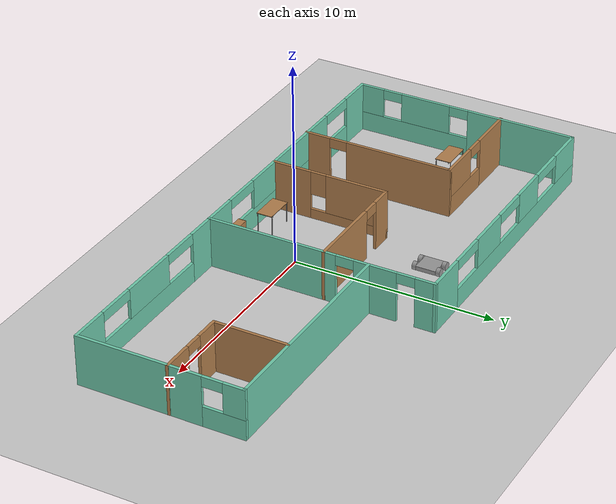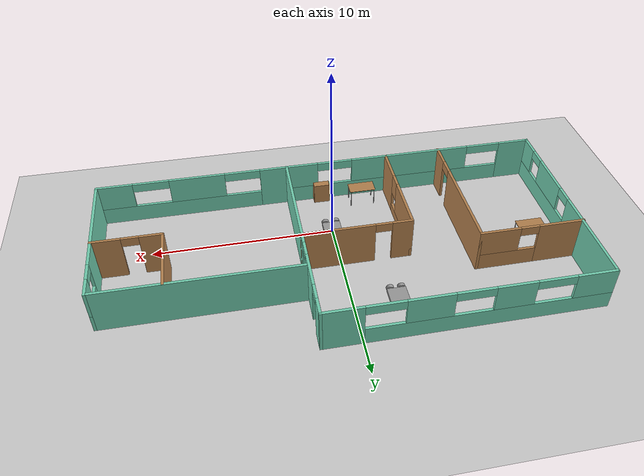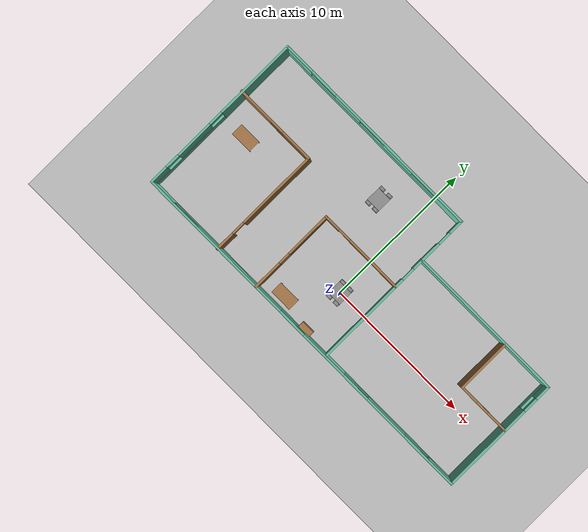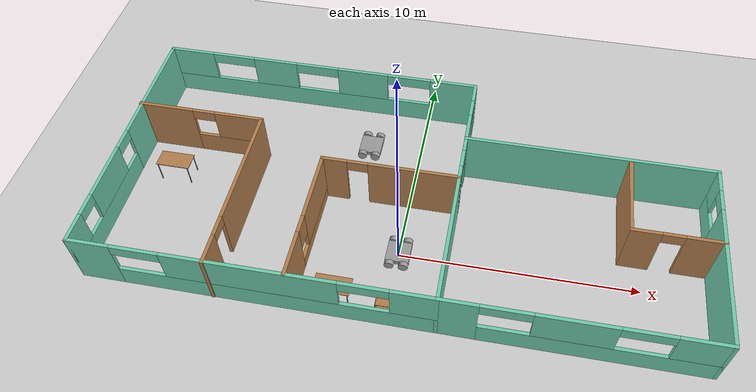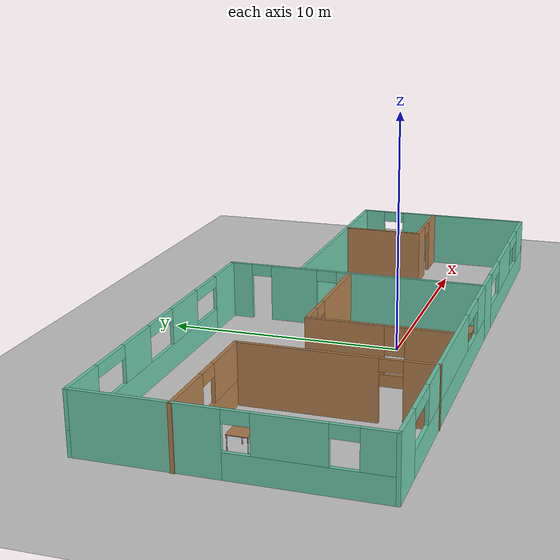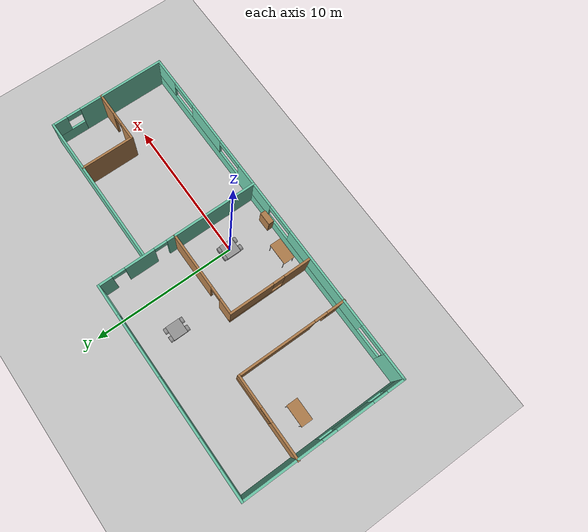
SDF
<sdf version="1.6">
 <world name="default">
  <plugin name="welcome" filename="libwelcome.so"/>
  <light name="sun" type="directional">
   <pose>0 0 10 0 -0 0</pose>
   <diffuse>0.8 0.8 0.8 1</diffuse>
   <specular>0.2 0.2 0.2 1</specular>
   <attenuation>
    <range>1000</range>
    <constant>0.9</constant>
    <linear>0.01</linear>
    <quadratic>0.001</quadratic>
   </attenuation>
   <direction>-0.5 0.1 -0.9</direction>
  </light>
  <model name="ground_plane">
   <static>1</static>
   <link name="link">
    <collision name="collision">
     <geometry><plane><normal>0 0 1</normal><size>100 100</size></plane></geometry>
     <surface><friction><ode><mu>100</mu><mu2>50</mu2></ode></friction></surface>
    </collision>
    <visual name="visual">
     <cast_shadows>0</cast_shadows>
     <geometry><plane><normal>0 0 1</normal><size>100 100</size></plane></geometry>
     <material>
      <script><uri>file://media/materials/scripts/gazebo.material</uri><name>Gazebo/Grey</name></script>
     </material>
    </visual>
   </link>
  </model>
  <gravity>0 0 -9.8</gravity>
  <magnetic_field>6e-06 2.3e-05 -4.2e-05</magnetic_field>
  <atmosphere type="adiabatic"/>
  <physics name="default_physics" default="0" type="ode">
   <max_step_size>0.001</max_step_size>
   <real_time_factor>1</real_time_factor>
   <real_time_update_rate>1000</real_time_update_rate>
  </physics>
  <scene><ambient>0.4 0.4 0.4 1</ambient><background>0.7 0.7 0.7 1</background><shadows>1</shadows></scene>
  <spherical_coordinates>
   <surface_model>EARTH_WGS84</surface_model>
   <latitude_deg>0</latitude_deg>
   <longitude_deg>0</longitude_deg>
   <elevation>0</elevation>
   <heading_deg>0</heading_deg>
  </spherical_coordinates>
  <model name="Building">
   <pose>0.0487 2.43488 0 0 -0 0</pose>
   <link name="Wall_16">
    <pose>-3.82517 -2.7038 0 0 -0 1.5708</pose>
    <visual name="Wall_16_Visual_0">
     <pose>-1.99039 0 1.25 0 -0 0</pose>
     <geometry><box><size>2.01921 0.15 2.5</size></box></geometry>
     <material>
      <script><uri>file://media/materials/scripts/gazebo.material</uri><name>Gazebo/Wood</name></script>
      <ambient>1 1 1 1</ambient>
     </material>
     <meta><layer>0</layer></meta>
    </visual>
    <collision name="Wall_16_Collision_0">
     <geometry><box><size>2.01921 0.15 2.5</size></box></geometry>
     <pose>-1.99039 0 1.25 0 -0 0</pose>
    </collision>
    <visual name="Wall_16_Visual_1">
     <pose>1.00961 0 0.25 0 -0 0</pose>
     <geometry><box><size>3.98079 0.15 0.5</size></box></geometry>
     <material>
      <script><uri>file://media/materials/scripts/gazebo.material</uri><name>Gazebo/Wood</name></script>
      <ambient>1 1 1 1</ambient>
     </material>
     <meta><layer>0</layer></meta>
    </visual>
    <collision name="Wall_16_Collision_1">
     <geometry><box><size>3.98079 0.15 0.5</size></box></geometry>
     <pose>1.00961 0 0.25 0 -0 0</pose>
    </collision>
    <visual name="Wall_16_Visual_2">
     <pose>1.4096 0 1.5 0 -0 0</pose>
     <geometry><box><size>3.18079 0.15 2</size></box></geometry>
     <material>
      <script><uri>file://media/materials/scripts/gazebo.material</uri><name>Gazebo/Wood</name></script>
      <ambient>1 1 1 1</ambient>
     </material>
     <meta><layer>0</layer></meta>
    </visual>
    <collision name="Wall_16_Collision_2">
     <geometry><box><size>3.18079 0.15 2</size></box></geometry>
     <pose>1.4096 0 1.5 0 -0 0</pose>
    </collision>
    <visual name="Wall_16_Visual_3">
     <pose>-0.580791 0 1.9 0 -0 0</pose>
     <geometry><box><size>0.8 0.15 1.2</size></box></geometry>
     <material>
      <script><uri>file://media/materials/scripts/gazebo.material</uri><name>Gazebo/Wood</name></script>
      <ambient>1 1 1 1</ambient>
     </material>
     <meta><layer>0</layer></meta>
    </visual>
    <collision name="Wall_16_Collision_3">
     <geometry><box><size>0.8 0.15 1.2</size></box></geometry>
     <pose>-0.580791 0 1.9 0 -0 0</pose>
    </collision>
   </link>
   <link name="Wall_17">
    <pose>-0.900166 0.221202 0 0 -0 0</pose>
    <visual name="Wall_17_Visual_0">
     <pose>-2.42762 0 1.25 0 -0 0</pose>
     <geometry><box><size>1.14476 0.15 2.5</size></box></geometry>
     <material>
      <script><uri>file://media/materials/scripts/gazebo.material</uri><name>Gazebo/Wood</name></script>
      <ambient>1 1 1 1</ambient>
     </material>
     <meta><layer>0</layer></meta>
    </visual>
    <collision name="Wall_17_Collision_0">
     <geometry><box><size>1.14476 0.15 2.5</size></box></geometry>
     <pose>-2.42762 0 1.25 0 -0 0</pose>
    </collision>
    <visual name="Wall_17_Visual_1">
     <pose>1.02238 0 1.25 0 -0 0</pose>
     <geometry><box><size>3.95524 0.15 2.5</size></box></geometry>
     <material>
      <script><uri>file://media/materials/scripts/gazebo.material</uri><name>Gazebo/Wood</name></script>
      <ambient>1 1 1 1</ambient>
     </material>
     <meta><layer>0</layer></meta>
    </visual>
    <collision name="Wall_17_Collision_1">
     <geometry><box><size>3.95524 0.15 2.5</size></box></geometry>
     <pose>1.02238 0 1.25 0 -0 0</pose>
    </collision>
    <visual name="Wall_17_Visual_2">
     <pose>-1.40524 0 2.25 0 -0 0</pose>
     <geometry><box><size>0.9 0.15 0.5</size></box></geometry>
     <material>
      <script><uri>file://media/materials/scripts/gazebo.material</uri><name>Gazebo/Wood</name></script>
      <ambient>1 1 1 1</ambient>
     </material>
     <meta><layer>0</layer></meta>
    </visual>
    <collision name="Wall_17_Collision_2">
     <geometry><box><size>0.9 0.15 0.5</size></box></geometry>
     <pose>-1.40524 0 2.25 0 -0 0</pose>
    </collision>
   </link>
   <link name="Wall_23">
    <pose>7.32067 -5.66058 0 0 -0 0</pose>
    <visual name="Wall_23_Visual_0">
     <pose>-4.56131 0 1.25 0 -0 0</pose>
     <geometry><box><size>1.62738 0.15 2.5</size></box></geometry>
     <material>
      <script><uri>file://media/materials/scripts/gazebo.material</uri><name>Gazebo/Grey</name></script>
      <ambient>0.435294 0.796078 0.67451 1</ambient>
     </material>
     <meta><layer>0</layer></meta>
    </visual>
    <collision name="Wall_23_Collision_0">
     <geometry><box><size>1.62738 0.15 2.5</size></box></geometry>
     <pose>-4.56131 0 1.25 0 -0 0</pose>
    </collision>
    <visual name="Wall_23_Visual_1">
     <pose>0.81369 0 0.5 0 -0 0</pose>
     <geometry><box><size>9.12262 0.15 1</size></box></geometry>
     <material>
      <script><uri>file://media/materials/scripts/gazebo.material</uri><name>Gazebo/Grey</name></script>
      <ambient>0.435294 0.796078 0.67451 1</ambient>
     </material>
     <meta><layer>0</layer></meta>
    </visual>
    <collision name="Wall_23_Collision_1">
     <geometry><box><size>9.12262 0.15 1</size></box></geometry>
     <pose>0.81369 0 0.5 0 -0 0</pose>
    </collision>
    <visual name="Wall_23_Visual_2">
     <pose>-0.193336 0 1.75 0 -0 0</pose>
     <geometry><box><size>3.10857 0.15 1.5</size></box></geometry>
     <material>
      <script><uri>file://media/materials/scripts/gazebo.material</uri><name>Gazebo/Grey</name></script>
      <ambient>0.435294 0.796078 0.67451 1</ambient>
     </material>
     <meta><layer>0</layer></meta>
    </visual>
    <collision name="Wall_23_Collision_2">
     <geometry><box><size>3.10857 0.15 1.5</size></box></geometry>
     <pose>-0.193336 0 1.75 0 -0 0</pose>
    </collision>
    <visual name="Wall_23_Visual_3">
     <pose>4.36797 0 1.75 0 -0 0</pose>
     <geometry><box><size>2.01405 0.15 1.5</size></box></geometry>
     <material>
      <script><uri>file://media/materials/scripts/gazebo.material</uri><name>Gazebo/Grey</name></script>
      <ambient>0.435294 0.796078 0.67451 1</ambient>
     </material>
     <meta><layer>0</layer></meta>
    </visual>
    <collision name="Wall_23_Collision_3">
     <geometry><box><size>2.01405 0.15 1.5</size></box></geometry>
     <pose>4.36797 0 1.75 0 -0 0</pose>
    </collision>
    <visual name="Wall_23_Visual_4">
     <pose>-2.74762 0 2.25 0 -0 0</pose>
     <geometry><box><size>2 0.15 0.5</size></box></geometry>
     <material>
      <script><uri>file://media/materials/scripts/gazebo.material</uri><name>Gazebo/Grey</name></script>
      <ambient>0.435294 0.796078 0.67451 1</ambient>
     </material>
     <meta><layer>0</layer></meta>
    </visual>
    <collision name="Wall_23_Collision_4">
     <geometry><box><size>2 0.15 0.5</size></box></geometry>
     <pose>-2.74762 0 2.25 0 -0 0</pose>
    </collision>
    <visual name="Wall_23_Visual_5">
     <pose>2.36095 0 2.25 0 -0 0</pose>
     <geometry><box><size>2 0.15 0.5</size></box></geometry>
     <material>
      <script><uri>file://media/materials/scripts/gazebo.material</uri><name>Gazebo/Grey</name></script>
      <ambient>0.435294 0.796078 0.67451 1</ambient>
     </material>
     <meta><layer>0</layer></meta>
    </visual>
    <collision name="Wall_23_Collision_5">
     <geometry><box><size>2 0.15 0.5</size></box></geometry>
     <pose>2.36095 0 2.25 0 -0 0</pose>
    </collision>
   </link>
   <link name="Wall_24">
    <pose>12.6207 -1.61058 0 0 -0 1.5708</pose>
    <visual name="Wall_24_Visual_0">
     <pose>-1.03878 0 1.25 0 -0 0</pose>
     <geometry><box><size>6.17244 0.15 2.5</size></box></geometry>
     <material>
      <script><uri>file://media/materials/scripts/gazebo.material</uri><name>Gazebo/Grey</name></script>
      <ambient>0.435294 0.796078 0.67451 1</ambient>
     </material>
     <meta><layer>0</layer></meta>
    </visual>
    <collision name="Wall_24_Collision_0">
     <geometry><box><size>6.17244 0.15 2.5</size></box></geometry>
     <pose>-1.03878 0 1.25 0 -0 0</pose>
    </collision>
    <visual name="Wall_24_Visual_1">
     <pose>3.08622 0 0.5 0 -0 0</pose>
     <geometry><box><size>2.07756 0.15 1</size></box></geometry>
     <material>
      <script><uri>file://media/materials/scripts/gazebo.material</uri><name>Gazebo/Grey</name></script>
      <ambient>0.435294 0.796078 0.67451 1</ambient>
     </material>
     <meta><layer>0</layer></meta>
    </visual>
    <collision name="Wall_24_Collision_1">
     <geometry><box><size>2.07756 0.15 1</size></box></geometry>
     <pose>3.08622 0 0.5 0 -0 0</pose>
    </collision>
    <visual name="Wall_24_Visual_2">
     <pose>3.58622 0 1.75 0 -0 0</pose>
     <geometry><box><size>1.07756 0.15 1.5</size></box></geometry>
     <material>
      <script><uri>file://media/materials/scripts/gazebo.material</uri><name>Gazebo/Grey</name></script>
      <ambient>0.435294 0.796078 0.67451 1</ambient>
     </material>
     <meta><layer>0</layer></meta>
    </visual>
    <collision name="Wall_24_Collision_2">
     <geometry><box><size>1.07756 0.15 1.5</size></box></geometry>
     <pose>3.58622 0 1.75 0 -0 0</pose>
    </collision>
    <visual name="Wall_24_Visual_3">
     <pose>2.54744 0 2.25 0 -0 0</pose>
     <geometry><box><size>1 0.15 0.5</size></box></geometry>
     <material>
      <script><uri>file://media/materials/scripts/gazebo.material</uri><name>Gazebo/Grey</name></script>
      <ambient>0.435294 0.796078 0.67451 1</ambient>
     </material>
     <meta><layer>0</layer></meta>
    </visual>
    <collision name="Wall_24_Collision_3">
     <geometry><box><size>1 0.15 0.5</size></box></geometry>
     <pose>2.54744 0 2.25 0 -0 0</pose>
    </collision>
   </link>
   <link name="Wall_25">
    <collision name="Wall_25_Collision">
     <geometry><box><size>10.75 0.15 2.5</size></box></geometry>
     <pose>0 0 1.25 0 -0 0</pose>
    </collision>
    <visual name="Wall_25_Visual">
     <pose>0 0 1.25 0 -0 0</pose>
     <geometry><box><size>10.75 0.15 2.5</size></box></geometry>
     <material>
      <script><uri>file://media/materials/scripts/gazebo.material</uri><name>Gazebo/Grey</name></script>
      <ambient>0.435294 0.796078 0.67451 1</ambient>
     </material>
     <meta><layer>0</layer></meta>
    </visual>
    <pose>7.32067 2.43942 0 0 -0 3.14159</pose>
   </link>
   <link name="Wall_27">
    <collision name="Wall_27_Collision">
     <geometry><box><size>3.75 0.15 2.5</size></box></geometry>
     <pose>0 0 1.25 0 -0 0</pose>
    </collision>
    <visual name="Wall_27_Visual">
     <pose>0 0 1.25 0 -0 0</pose>
     <geometry><box><size>3.75 0.15 2.5</size></box></geometry>
     <material>
      <script><uri>file://media/materials/scripts/gazebo.material</uri><name>Gazebo/Wood</name></script>
      <ambient>1 1 1 1</ambient>
     </material>
     <meta><layer>0</layer></meta>
    </visual>
    <pose>9.02628 0.615984 0 0 0 -1.5708</pose>
   </link>
   <link name="Wall_28">
    <pose>10.8263 -1.18402 0 0 -0 0</pose>
    <visual name="Wall_28_Visual_0">
     <pose>-1.23789 0 1.25 0 -0 0</pose>
     <geometry><box><size>1.27421 0.15 2.5</size></box></geometry>
     <material>
      <script><uri>file://media/materials/scripts/gazebo.material</uri><name>Gazebo/Wood</name></script>
      <ambient>1 1 1 1</ambient>
     </material>
     <meta><layer>0</layer></meta>
    </visual>
    <collision name="Wall_28_Collision_0">
     <geometry><box><size>1.27421 0.15 2.5</size></box></geometry>
     <pose>-1.23789 0 1.25 0 -0 0</pose>
    </collision>
    <visual name="Wall_28_Visual_1">
     <pose>1.08711 0 1.25 0 -0 0</pose>
     <geometry><box><size>1.57579 0.15 2.5</size></box></geometry>
     <material>
      <script><uri>file://media/materials/scripts/gazebo.material</uri><name>Gazebo/Wood</name></script>
      <ambient>1 1 1 1</ambient>
     </material>
     <meta><layer>0</layer></meta>
    </visual>
    <collision name="Wall_28_Collision_1">
     <geometry><box><size>1.57579 0.15 2.5</size></box></geometry>
     <pose>1.08711 0 1.25 0 -0 0</pose>
    </collision>
    <visual name="Wall_28_Visual_2">
     <pose>-0.150787 0 2.25 0 -0 0</pose>
     <geometry><box><size>0.9 0.15 0.5</size></box></geometry>
     <material>
      <script><uri>file://media/materials/scripts/gazebo.material</uri><name>Gazebo/Wood</name></script>
      <ambient>1 1 1 1</ambient>
     </material>
     <meta><layer>0</layer></meta>
    </visual>
    <collision name="Wall_28_Collision_2">
     <geometry><box><size>0.9 0.15 0.5</size></box></geometry>
     <pose>-0.150787 0 2.25 0 -0 0</pose>
    </collision>
   </link>
   <link name="Wall_30">
    <pose>-9.82628 1.91058 0 0 -0 0</pose>
    <visual name="Wall_30_Visual_0">
     <pose>-1.61536 0 1.25 0 -0 0</pose>
     <geometry><box><size>2.51928 0.15 2.5</size></box></geometry>
     <material>
      <script><uri>file://media/materials/scripts/gazebo.material</uri><name>Gazebo/Wood</name></script>
      <ambient>1 1 1 1</ambient>
     </material>
     <meta><layer>0</layer></meta>
    </visual>
    <collision name="Wall_30_Collision_0">
     <geometry><box><size>2.51928 0.15 2.5</size></box></geometry>
     <pose>-1.61536 0 1.25 0 -0 0</pose>
    </collision>
    <visual name="Wall_30_Visual_1">
     <pose>1.25964 0 0.5 0 -0 0</pose>
     <geometry><box><size>3.23072 0.15 1</size></box></geometry>
     <material>
      <script><uri>file://media/materials/scripts/gazebo.material</uri><name>Gazebo/Wood</name></script>
      <ambient>1 1 1 1</ambient>
     </material>
     <meta><layer>0</layer></meta>
    </visual>
    <collision name="Wall_30_Collision_1">
     <geometry><box><size>3.23072 0.15 1</size></box></geometry>
     <pose>1.25964 0 0.5 0 -0 0</pose>
    </collision>
    <visual name="Wall_30_Visual_2">
     <pose>1.75964 0 1.75 0 -0 0</pose>
     <geometry><box><size>2.23072 0.15 1.5</size></box></geometry>
     <material>
      <script><uri>file://media/materials/scripts/gazebo.material</uri><name>Gazebo/Wood</name></script>
      <ambient>1 1 1 1</ambient>
     </material>
     <meta><layer>0</layer></meta>
    </visual>
    <collision name="Wall_30_Collision_2">
     <geometry><box><size>2.23072 0.15 1.5</size></box></geometry>
     <pose>1.75964 0 1.75 0 -0 0</pose>
    </collision>
    <visual name="Wall_30_Visual_3">
     <pose>0.144283 0 2.25 0 -0 0</pose>
     <geometry><box><size>1 0.15 0.5</size></box></geometry>
     <material>
      <script><uri>file://media/materials/scripts/gazebo.material</uri><name>Gazebo/Wood</name></script>
      <ambient>1 1 1 1</ambient>
     </material>
     <meta><layer>0</layer></meta>
    </visual>
    <collision name="Wall_30_Collision_3">
     <geometry><box><size>1 0.15 0.5</size></box></geometry>
     <pose>0.144283 0 2.25 0 -0 0</pose>
    </collision>
   </link>
   <link name="Wall_33">
    <pose>-7.02628 -1.88942 0 0 0 -1.5708</pose>
    <visual name="Wall_33_Visual_0">
     <pose>-1.12318 0 1.25 0 -0 0</pose>
     <geometry><box><size>5.50364 0.15 2.5</size></box></geometry>
     <material>
      <script><uri>file://media/materials/scripts/gazebo.material</uri><name>Gazebo/Wood</name></script>
      <ambient>1 1 1 1</ambient>
     </material>
     <meta><layer>0</layer></meta>
    </visual>
    <collision name="Wall_33_Collision_0">
     <geometry><box><size>5.50364 0.15 2.5</size></box></geometry>
     <pose>-1.12318 0 1.25 0 -0 0</pose>
    </collision>
    <visual name="Wall_33_Visual_1">
     <pose>3.20182 0 1.25 0 -0 0</pose>
     <geometry><box><size>1.34636 0.15 2.5</size></box></geometry>
     <material>
      <script><uri>file://media/materials/scripts/gazebo.material</uri><name>Gazebo/Wood</name></script>
      <ambient>1 1 1 1</ambient>
     </material>
     <meta><layer>0</layer></meta>
    </visual>
    <collision name="Wall_33_Collision_1">
     <geometry><box><size>1.34636 0.15 2.5</size></box></geometry>
     <pose>3.20182 0 1.25 0 -0 0</pose>
    </collision>
    <visual name="Wall_33_Visual_2">
     <pose>2.07864 0 2.25 0 -0 0</pose>
     <geometry><box><size>0.9 0.15 0.5</size></box></geometry>
     <material>
      <script><uri>file://media/materials/scripts/gazebo.material</uri><name>Gazebo/Wood</name></script>
      <ambient>1 1 1 1</ambient>
     </material>
     <meta><layer>0</layer></meta>
    </visual>
    <collision name="Wall_33_Collision_2">
     <geometry><box><size>0.9 0.15 0.5</size></box></geometry>
     <pose>2.07864 0 2.25 0 -0 0</pose>
    </collision>
   </link>
   <link name="Wall_4">
    <pose>-12.5793 0.01442 0 0 0 -1.5708</pose>
    <visual name="Wall_4_Visual_0">
     <pose>-2.95936 0 1.25 0 -0 0</pose>
     <geometry><box><size>5.58129 0.15 2.5</size></box></geometry>
     <material>
      <script><uri>file://media/materials/scripts/gazebo.material</uri><name>Gazebo/Grey</name></script>
      <ambient>0.435294 0.796078 0.67451 1</ambient>
     </material>
     <meta><layer>0</layer></meta>
    </visual>
    <collision name="Wall_4_Collision_0">
     <geometry><box><size>5.58129 0.15 2.5</size></box></geometry>
     <pose>-2.95936 0 1.25 0 -0 0</pose>
    </collision>
    <visual name="Wall_4_Visual_1">
     <pose>2.79064 0 0.5 0 -0 0</pose>
     <geometry><box><size>5.91871 0.15 1</size></box></geometry>
     <material>
      <script><uri>file://media/materials/scripts/gazebo.material</uri><name>Gazebo/Grey</name></script>
      <ambient>0.435294 0.796078 0.67451 1</ambient>
     </material>
     <meta><layer>0</layer></meta>
    </visual>
    <collision name="Wall_4_Collision_1">
     <geometry><box><size>5.91871 0.15 1</size></box></geometry>
     <pose>2.79064 0 0.5 0 -0 0</pose>
    </collision>
    <visual name="Wall_4_Visual_2">
     <pose>2.13634 0 1.75 0 -0 0</pose>
     <geometry><box><size>2.61011 0.15 1.5</size></box></geometry>
     <material>
      <script><uri>file://media/materials/scripts/gazebo.material</uri><name>Gazebo/Grey</name></script>
      <ambient>0.435294 0.796078 0.67451 1</ambient>
     </material>
     <meta><layer>0</layer></meta>
    </visual>
    <collision name="Wall_4_Collision_2">
     <geometry><box><size>2.61011 0.15 1.5</size></box></geometry>
     <pose>2.13634 0 1.75 0 -0 0</pose>
    </collision>
    <visual name="Wall_4_Visual_3">
     <pose>5.0957 0 1.75 0 -0 0</pose>
     <geometry><box><size>1.3086 0.15 1.5</size></box></geometry>
     <material>
      <script><uri>file://media/materials/scripts/gazebo.material</uri><name>Gazebo/Grey</name></script>
      <ambient>0.435294 0.796078 0.67451 1</ambient>
     </material>
     <meta><layer>0</layer></meta>
    </visual>
    <collision name="Wall_4_Collision_3">
     <geometry><box><size>1.3086 0.15 1.5</size></box></geometry>
     <pose>5.0957 0 1.75 0 -0 0</pose>
    </collision>
    <visual name="Wall_4_Visual_4">
     <pose>0.331288 0 2.25 0 -0 0</pose>
     <geometry><box><size>1 0.15 0.5</size></box></geometry>
     <material>
      <script><uri>file://media/materials/scripts/gazebo.material</uri><name>Gazebo/Grey</name></script>
      <ambient>0.435294 0.796078 0.67451 1</ambient>
     </material>
     <meta><layer>0</layer></meta>
    </visual>
    <collision name="Wall_4_Collision_4">
     <geometry><box><size>1 0.15 0.5</size></box></geometry>
     <pose>0.331288 0 2.25 0 -0 0</pose>
    </collision>
    <visual name="Wall_4_Visual_5">
     <pose>3.9414 0 2.25 0 -0 0</pose>
     <geometry><box><size>1 0.15 0.5</size></box></geometry>
     <material>
      <script><uri>file://media/materials/scripts/gazebo.material</uri><name>Gazebo/Grey</name></script>
      <ambient>0.435294 0.796078 0.67451 1</ambient>
     </material>
     <meta><layer>0</layer></meta>
    </visual>
    <collision name="Wall_4_Collision_5">
     <geometry><box><size>1 0.15 0.5</size></box></geometry>
     <pose>3.9414 0 2.25 0 -0 0</pose>
    </collision>
   </link>
   <link name="Wall_5">
    <pose>-5.27933 -5.66058 0 0 -0 0</pose>
    <visual name="Wall_5_Visual_0">
     <pose>-6.45001 0 1.25 0 -0 0</pose>
     <geometry><box><size>1.84997 0.15 2.5</size></box></geometry>
     <material>
      <script><uri>file://media/materials/scripts/gazebo.material</uri><name>Gazebo/Grey</name></script>
      <ambient>0.435294 0.796078 0.67451 1</ambient>
     </material>
     <meta><layer>0</layer></meta>
    </visual>
    <collision name="Wall_5_Collision_0">
     <geometry><box><size>1.84997 0.15 2.5</size></box></geometry>
     <pose>-6.45001 0 1.25 0 -0 0</pose>
    </collision>
    <visual name="Wall_5_Visual_1">
     <pose>0.924986 0 0.5 0 -0 0</pose>
     <geometry><box><size>12.9 0.15 1</size></box></geometry>
     <material>
      <script><uri>file://media/materials/scripts/gazebo.material</uri><name>Gazebo/Grey</name></script>
      <ambient>0.435294 0.796078 0.67451 1</ambient>
     </material>
     <meta><layer>0</layer></meta>
    </visual>
    <collision name="Wall_5_Collision_1">
     <geometry><box><size>12.9 0.15 1</size></box></geometry>
     <pose>0.924986 0 0.5 0 -0 0</pose>
    </collision>
    <visual name="Wall_5_Visual_2">
     <pose>-0.012969 0 1.75 0 -0 0</pose>
     <geometry><box><size>7.02412 0.15 1.5</size></box></geometry>
     <material>
      <script><uri>file://media/materials/scripts/gazebo.material</uri><name>Gazebo/Grey</name></script>
      <ambient>0.435294 0.796078 0.67451 1</ambient>
     </material>
     <meta><layer>0</layer></meta>
    </visual>
    <collision name="Wall_5_Collision_2">
     <geometry><box><size>7.02412 0.15 1.5</size></box></geometry>
     <pose>-0.012969 0 1.75 0 -0 0</pose>
    </collision>
    <visual name="Wall_5_Visual_3">
     <pose>6.43705 0 1.75 0 -0 0</pose>
     <geometry><box><size>1.87591 0.15 1.5</size></box></geometry>
     <material>
      <script><uri>file://media/materials/scripts/gazebo.material</uri><name>Gazebo/Grey</name></script>
      <ambient>0.435294 0.796078 0.67451 1</ambient>
     </material>
     <meta><layer>0</layer></meta>
    </visual>
    <collision name="Wall_5_Collision_3">
     <geometry><box><size>1.87591 0.15 1.5</size></box></geometry>
     <pose>6.43705 0 1.75 0 -0 0</pose>
    </collision>
    <visual name="Wall_5_Visual_4">
     <pose>-4.52503 0 2.25 0 -0 0</pose>
     <geometry><box><size>2 0.15 0.5</size></box></geometry>
     <material>
      <script><uri>file://media/materials/scripts/gazebo.material</uri><name>Gazebo/Grey</name></script>
      <ambient>0.435294 0.796078 0.67451 1</ambient>
     </material>
     <meta><layer>0</layer></meta>
    </visual>
    <collision name="Wall_5_Collision_4">
     <geometry><box><size>2 0.15 0.5</size></box></geometry>
     <pose>-4.52503 0 2.25 0 -0 0</pose>
    </collision>
    <visual name="Wall_5_Visual_5">
     <pose>4.49909 0 2.25 0 -0 0</pose>
     <geometry><box><size>2 0.15 0.5</size></box></geometry>
     <material>
      <script><uri>file://media/materials/scripts/gazebo.material</uri><name>Gazebo/Grey</name></script>
      <ambient>0.435294 0.796078 0.67451 1</ambient>
     </material>
     <meta><layer>0</layer></meta>
    </visual>
    <collision name="Wall_5_Collision_5">
     <geometry><box><size>2 0.15 0.5</size></box></geometry>
     <pose>4.49909 0 2.25 0 -0 0</pose>
    </collision>
   </link>
   <link name="Wall_6">
    <pose>2.02067 0.01442 0 0 -0 1.5708</pose>
    <visual name="Wall_6_Visual_0">
     <pose>-2.47112 0 1.25 0 -0 0</pose>
     <geometry><box><size>6.55776 0.15 2.5</size></box></geometry>
     <material>
      <script><uri>file://media/materials/scripts/gazebo.material</uri><name>Gazebo/Grey</name></script>
      <ambient>0.435294 0.796078 0.67451 1</ambient>
     </material>
     <meta><layer>0</layer></meta>
    </visual>
    <collision name="Wall_6_Collision_0">
     <geometry><box><size>6.55776 0.15 2.5</size></box></geometry>
     <pose>-2.47112 0 1.25 0 -0 0</pose>
    </collision>
    <visual name="Wall_6_Visual_1">
     <pose>2.76067 0 1.25 0 -0 0</pose>
     <geometry><box><size>2.10582 0.15 2.5</size></box></geometry>
     <material>
      <script><uri>file://media/materials/scripts/gazebo.material</uri><name>Gazebo/Grey</name></script>
      <ambient>0.435294 0.796078 0.67451 1</ambient>
     </material>
     <meta><layer>0</layer></meta>
    </visual>
    <collision name="Wall_6_Collision_1">
     <geometry><box><size>2.10582 0.15 2.5</size></box></geometry>
     <pose>2.76067 0 1.25 0 -0 0</pose>
    </collision>
    <visual name="Wall_6_Visual_2">
     <pose>5.23179 0 1.25 0 -0 0</pose>
     <geometry><box><size>1.03642 0.15 2.5</size></box></geometry>
     <material>
      <script><uri>file://media/materials/scripts/gazebo.material</uri><name>Gazebo/Grey</name></script>
      <ambient>0.435294 0.796078 0.67451 1</ambient>
     </material>
     <meta><layer>0</layer></meta>
    </visual>
    <collision name="Wall_6_Collision_2">
     <geometry><box><size>1.03642 0.15 2.5</size></box></geometry>
     <pose>5.23179 0 1.25 0 -0 0</pose>
    </collision>
    <visual name="Wall_6_Visual_3">
     <pose>1.25776 0 2.25 0 -0 0</pose>
     <geometry><box><size>0.9 0.15 0.5</size></box></geometry>
     <material>
      <script><uri>file://media/materials/scripts/gazebo.material</uri><name>Gazebo/Grey</name></script>
      <ambient>0.435294 0.796078 0.67451 1</ambient>
     </material>
     <meta><layer>0</layer></meta>
    </visual>
    <collision name="Wall_6_Collision_3">
     <geometry><box><size>0.9 0.15 0.5</size></box></geometry>
     <pose>1.25776 0 2.25 0 -0 0</pose>
    </collision>
    <visual name="Wall_6_Visual_4">
     <pose>4.26358 0 2.25 0 -0 0</pose>
     <geometry><box><size>0.9 0.15 0.5</size></box></geometry>
     <material>
      <script><uri>file://media/materials/scripts/gazebo.material</uri><name>Gazebo/Grey</name></script>
      <ambient>0.435294 0.796078 0.67451 1</ambient>
     </material>
     <meta><layer>0</layer></meta>
    </visual>
    <collision name="Wall_6_Collision_4">
     <geometry><box><size>0.9 0.15 0.5</size></box></geometry>
     <pose>4.26358 0 2.25 0 -0 0</pose>
    </collision>
   </link>
   <link name="Wall_7">
    <pose>-5.27933 5.68942 0 0 -0 3.14159</pose>
    <visual name="Wall_7_Visual_0">
     <pose>-6.28409 0 1.25 0 -0 0</pose>
     <geometry><box><size>2.18181 0.15 2.5</size></box></geometry>
     <material>
      <script><uri>file://media/materials/scripts/gazebo.material</uri><name>Gazebo/Grey</name></script>
      <ambient>0.435294 0.796078 0.67451 1</ambient>
     </material>
     <meta><layer>0</layer></meta>
    </visual>
    <collision name="Wall_7_Collision_0">
     <geometry><box><size>2.18181 0.15 2.5</size></box></geometry>
     <pose>-6.28409 0 1.25 0 -0 0</pose>
    </collision>
    <visual name="Wall_7_Visual_1">
     <pose>1.09091 0 0.5 0 -0 0</pose>
     <geometry><box><size>12.5682 0.15 1</size></box></geometry>
     <material>
      <script><uri>file://media/materials/scripts/gazebo.material</uri><name>Gazebo/Grey</name></script>
      <ambient>0.435294 0.796078 0.67451 1</ambient>
     </material>
     <meta><layer>0</layer></meta>
    </visual>
    <collision name="Wall_7_Collision_1">
     <geometry><box><size>12.5682 0.15 1</size></box></geometry>
     <pose>1.09091 0 0.5 0 -0 0</pose>
    </collision>
    <visual name="Wall_7_Visual_2">
     <pose>-2.00599 0 1.75 0 -0 0</pose>
     <geometry><box><size>2.3744 0.15 1.5</size></box></geometry>
     <material>
      <script><uri>file://media/materials/scripts/gazebo.material</uri><name>Gazebo/Grey</name></script>
      <ambient>0.435294 0.796078 0.67451 1</ambient>
     </material>
     <meta><layer>0</layer></meta>
    </visual>
    <collision name="Wall_7_Collision_2">
     <geometry><box><size>2.3744 0.15 1.5</size></box></geometry>
     <pose>-2.00599 0 1.75 0 -0 0</pose>
    </collision>
    <visual name="Wall_7_Visual_3">
     <pose>2.21547 0 1.75 0 -0 0</pose>
     <geometry><box><size>2.0685 0.15 1.5</size></box></geometry>
     <material>
      <script><uri>file://media/materials/scripts/gazebo.material</uri><name>Gazebo/Grey</name></script>
      <ambient>0.435294 0.796078 0.67451 1</ambient>
     </material>
     <meta><layer>0</layer></meta>
    </visual>
    <collision name="Wall_7_Collision_3">
     <geometry><box><size>2.0685 0.15 1.5</size></box></geometry>
     <pose>2.21547 0 1.75 0 -0 0</pose>
    </collision>
    <visual name="Wall_7_Visual_4">
     <pose>6.31236 0 1.75 0 -0 0</pose>
     <geometry><box><size>2.12528 0.15 1.5</size></box></geometry>
     <material>
      <script><uri>file://media/materials/scripts/gazebo.material</uri><name>Gazebo/Grey</name></script>
      <ambient>0.435294 0.796078 0.67451 1</ambient>
     </material>
     <meta><layer>0</layer></meta>
    </visual>
    <collision name="Wall_7_Collision_4">
     <geometry><box><size>2.12528 0.15 1.5</size></box></geometry>
     <pose>6.31236 0 1.75 0 -0 0</pose>
    </collision>
    <visual name="Wall_7_Visual_5">
     <pose>-4.19319 0 2.25 0 -0 0</pose>
     <geometry><box><size>2 0.15 0.5</size></box></geometry>
     <material>
      <script><uri>file://media/materials/scripts/gazebo.material</uri><name>Gazebo/Grey</name></script>
      <ambient>0.435294 0.796078 0.67451 1</ambient>
     </material>
     <meta><layer>0</layer></meta>
    </visual>
    <collision name="Wall_7_Collision_5">
     <geometry><box><size>2 0.15 0.5</size></box></geometry>
     <pose>-4.19319 0 2.25 0 -0 0</pose>
    </collision>
    <visual name="Wall_7_Visual_6">
     <pose>0.181215 0 2.25 0 -0 0</pose>
     <geometry><box><size>2 0.15 0.5</size></box></geometry>
     <material>
      <script><uri>file://media/materials/scripts/gazebo.material</uri><name>Gazebo/Grey</name></script>
      <ambient>0.435294 0.796078 0.67451 1</ambient>
     </material>
     <meta><layer>0</layer></meta>
    </visual>
    <collision name="Wall_7_Collision_6">
     <geometry><box><size>2 0.15 0.5</size></box></geometry>
     <pose>0.181215 0 2.25 0 -0 0</pose>
    </collision>
    <visual name="Wall_7_Visual_7">
     <pose>4.24972 0 2.25 0 -0 0</pose>
     <geometry><box><size>2 0.15 0.5</size></box></geometry>
     <material>
      <script><uri>file://media/materials/scripts/gazebo.material</uri><name>Gazebo/Grey</name></script>
      <ambient>0.435294 0.796078 0.67451 1</ambient>
     </material>
     <meta><layer>0</layer></meta>
    </visual>
    <collision name="Wall_7_Collision_7">
     <geometry><box><size>2 0.15 0.5</size></box></geometry>
     <pose>4.24972 0 2.25 0 -0 0</pose>
    </collision>
   </link>
   <static>1</static>
  </model>
  <model name="HumanoidRobot">
   <link name="link_0">
    <pose>1.17962 -2.85179 0 0 -0 0</pose>
    <inertial>
     <mass>1</mass>
     <inertia>
      <ixx>0.166667</ixx>
      <ixy>0</ixy>
      <ixz>0</ixz>
      <iyy>0.166667</iyy>
      <iyz>0</iyz>
      <izz>0.166667</izz>
     </inertia>
    </inertial>
    <visual name="visual">
     <geometry><box><size>1 1 0.2</size></box></geometry>
     <material>
      <lighting>1</lighting>
      <script><uri>file://media/materials/scripts/gazebo.material</uri><name>Gazebo/Grey</name></script>
      <ambient>0.3 0.3 0.3 1</ambient>
      <diffuse>0.7 0.7 0.7 1</diffuse>
      <specular>0.01 0.01 0.01 1</specular>
      <emissive>0 0 0 1</emissive>
      <shader type="vertex"><normal_map>__default__</normal_map></shader>
     </material>
    </visual>
    <collision name="collision">
     <geometry><box><size>1 1 0.2</size></box></geometry>
     <surface>
      <friction>
       <ode><mu>1</mu><mu2>1</mu2><fdir1>0 0 0</fdir1><slip1>0</slip1><slip2>0</slip2></ode>
       <torsional>
        <coefficient>1</coefficient>
        <patch_radius>0</patch_radius>
        <surface_radius>0</surface_radius>
        <use_patch_radius>1</use_patch_radius>
        <ode><slip>0</slip></ode>
       </torsional>
      </friction>
      <bounce><restitution_coefficient>0</restitution_coefficient><threshold>1e+06</threshold></bounce>
      <contact>
       <collide_without_contact>0</collide_without_contact>
       <collide_without_contact_bitmask>1</collide_without_contact_bitmask>
       <collide_bitmask>1</collide_bitmask>
       <ode>
        <soft_cfm>0</soft_cfm>
        <soft_erp>0.2</soft_erp>
        <kp>1e+13</kp>
        <kd>1</kd>
        <max_vel>0.01</max_vel>
        <min_depth>0</min_depth>
       </ode>
       <bullet>
        <split_impulse>1</split_impulse>
        <split_impulse_penetration_threshold>-0.01</split_impulse_penetration_threshold>
        <soft_cfm>0</soft_cfm>
        <soft_erp>0.2</soft_erp>
        <kp>1e+13</kp>
        <kd>1</kd>
       </bullet>
      </contact>
     </surface>
    </collision>
   </link>
   <link name="link_0_clone">
    <pose>-1.17962 2.85179 0 0 -0 0</pose>
    <inertial>
     <mass>1</mass>
     <inertia>
      <ixx>0.166667</ixx>
      <ixy>0</ixy>
      <ixz>0</ixz>
      <iyy>0.166667</iyy>
      <iyz>0</iyz>
      <izz>0.166667</izz>
     </inertia>
    </inertial>
    <visual name="visual">
     <geometry><box><size>1 1 0.2</size></box></geometry>
     <material>
      <lighting>1</lighting>
      <script><uri>file://media/materials/scripts/gazebo.material</uri><name>Gazebo/Grey</name></script>
      <ambient>0.3 0.3 0.3 1</ambient>
      <diffuse>0.7 0.7 0.7 1</diffuse>
      <specular>0.01 0.01 0.01 1</specular>
      <emissive>0 0 0 1</emissive>
      <shader type="vertex"><normal_map>__default__</normal_map></shader>
     </material>
    </visual>
    <collision name="collision">
     <geometry><box><size>1 1 0.2</size></box></geometry>
     <surface>
      <friction>
       <ode><mu>1</mu><mu2>1</mu2><fdir1>0 0 0</fdir1><slip1>0</slip1><slip2>0</slip2></ode>
       <torsional>
        <coefficient>1</coefficient>
        <patch_radius>0</patch_radius>
        <surface_radius>0</surface_radius>
        <use_patch_radius>1</use_patch_radius>
        <ode><slip>0</slip></ode>
       </torsional>
      </friction>
      <bounce><restitution_coefficient>0</restitution_coefficient><threshold>1e+06</threshold></bounce>
      <contact>
       <collide_without_contact>0</collide_without_contact>
       <collide_without_contact_bitmask>1</collide_without_contact_bitmask>
       <collide_bitmask>1</collide_bitmask>
       <ode>
        <soft_cfm>0</soft_cfm>
        <soft_erp>0.2</soft_erp>
        <kp>1e+13</kp>
        <kd>1</kd>
        <max_vel>0.01</max_vel>
        <min_depth>0</min_depth>
       </ode>
       <bullet>
        <split_impulse>1</split_impulse>
        <split_impulse_penetration_threshold>-0.01</split_impulse_penetration_threshold>
        <soft_cfm>0</soft_cfm>
        <soft_erp>0.2</soft_erp>
        <kp>1e+13</kp>
        <kd>1</kd>
       </bullet>
      </contact>
     </surface>
    </collision>
   </link>
   <link name="link_2_clone_1">
    <pose>0.879625 -3.45181 0 1.5707 -0 0</pose>
    <inertial>
     <mass>1</mass>
     <inertia><ixx>0.145833</ixx><ixy>0</ixy><ixz>0</ixz><iyy>0.145833</iyy><iyz>0</iyz><izz>0.125</izz></inertia>
    </inertial>
    <visual name="visual">
     <geometry><cylinder><radius>0.2</radius><length>0.2</length></cylinder></geometry>
     <material>
      <lighting>1</lighting>
      <script><uri>file://media/materials/scripts/gazebo.material</uri><name>Gazebo/Grey</name></script>
      <ambient>0.3 0.3 0.3 1</ambient>
      <diffuse>0.7 0.7 0.7 1</diffuse>
      <specular>0.01 0.01 0.01 1</specular>
      <emissive>0 0 0 1</emissive>
      <shader type="vertex"><normal_map>__default__</normal_map></shader>
     </material>
    </visual>
    <collision name="collision">
     <geometry><cylinder><radius>0.2</radius><length>0.2</length></cylinder></geometry>
     <surface>
      <friction>
       <ode><mu>1</mu><mu2>1</mu2><fdir1>0 0 0</fdir1><slip1>0</slip1><slip2>0</slip2></ode>
       <torsional>
        <coefficient>1</coefficient>
        <patch_radius>0</patch_radius>
        <surface_radius>0</surface_radius>
        <use_patch_radius>1</use_patch_radius>
        <ode><slip>0</slip></ode>
       </torsional>
      </friction>
      <bounce><restitution_coefficient>0</restitution_coefficient><threshold>1e+06</threshold></bounce>
      <contact>
       <collide_without_contact>0</collide_without_contact>
       <collide_without_contact_bitmask>1</collide_without_contact_bitmask>
       <collide_bitmask>1</collide_bitmask>
       <ode>
        <soft_cfm>0</soft_cfm>
        <soft_erp>0.2</soft_erp>
        <kp>1e+13</kp>
        <kd>1</kd>
        <max_vel>0.01</max_vel>
        <min_depth>0</min_depth>
       </ode>
       <bullet>
        <split_impulse>1</split_impulse>
        <split_impulse_penetration_threshold>-0.01</split_impulse_penetration_threshold>
        <soft_cfm>0</soft_cfm>
        <soft_erp>0.2</soft_erp>
        <kp>1e+13</kp>
        <kd>1</kd>
       </bullet>
      </contact>
     </surface>
    </collision>
   </link>
   <link name="link_2_clone_1_clone">
    <pose>1.47962 -3.45181 0 1.5707 -0 0</pose>
    <inertial>
     <mass>1</mass>
     <inertia><ixx>0.145833</ixx><ixy>0</ixy><ixz>0</ixz><iyy>0.145833</iyy><iyz>0</iyz><izz>0.125</izz></inertia>
    </inertial>
    <visual name="visual">
     <geometry><cylinder><radius>0.2</radius><length>0.2</length></cylinder></geometry>
     <material>
      <lighting>1</lighting>
      <script><uri>file://media/materials/scripts/gazebo.material</uri><name>Gazebo/Grey</name></script>
      <ambient>0.3 0.3 0.3 1</ambient>
      <diffuse>0.7 0.7 0.7 1</diffuse>
      <specular>0.01 0.01 0.01 1</specular>
      <emissive>0 0 0 1</emissive>
      <shader type="vertex"><normal_map>__default__</normal_map></shader>
     </material>
    </visual>
    <collision name="collision">
     <geometry><cylinder><radius>0.2</radius><length>0.2</length></cylinder></geometry>
     <surface>
      <friction>
       <ode><mu>1</mu><mu2>1</mu2><fdir1>0 0 0</fdir1><slip1>0</slip1><slip2>0</slip2></ode>
       <torsional>
        <coefficient>1</coefficient>
        <patch_radius>0</patch_radius>
        <surface_radius>0</surface_radius>
        <use_patch_radius>1</use_patch_radius>
        <ode><slip>0</slip></ode>
       </torsional>
      </friction>
      <bounce><restitution_coefficient>0</restitution_coefficient><threshold>1e+06</threshold></bounce>
      <contact>
       <collide_without_contact>0</collide_without_contact>
       <collide_without_contact_bitmask>1</collide_without_contact_bitmask>
       <collide_bitmask>1</collide_bitmask>
       <ode>
        <soft_cfm>0</soft_cfm>
        <soft_erp>0.2</soft_erp>
        <kp>1e+13</kp>
        <kd>1</kd>
        <max_vel>0.01</max_vel>
        <min_depth>0</min_depth>
       </ode>
       <bullet>
        <split_impulse>1</split_impulse>
        <split_impulse_penetration_threshold>-0.01</split_impulse_penetration_threshold>
        <soft_cfm>0</soft_cfm>
        <soft_erp>0.2</soft_erp>
        <kp>1e+13</kp>
        <kd>1</kd>
       </bullet>
      </contact>
     </surface>
    </collision>
   </link>
   <link name="link_2_clone_1_clone_0">
    <pose>0.879625 -2.25177 0 1.5707 -0 0</pose>
    <inertial>
     <mass>1</mass>
     <inertia><ixx>0.145833</ixx><ixy>0</ixy><ixz>0</ixz><iyy>0.145833</iyy><iyz>0</iyz><izz>0.125</izz></inertia>
    </inertial>
    <visual name="visual">
     <geometry><cylinder><radius>0.2</radius><length>0.2</length></cylinder></geometry>
     <material>
      <lighting>1</lighting>
      <script><uri>file://media/materials/scripts/gazebo.material</uri><name>Gazebo/Grey</name></script>
      <ambient>0.3 0.3 0.3 1</ambient>
      <diffuse>0.7 0.7 0.7 1</diffuse>
      <specular>0.01 0.01 0.01 1</specular>
      <emissive>0 0 0 1</emissive>
      <shader type="vertex"><normal_map>__default__</normal_map></shader>
     </material>
    </visual>
    <collision name="collision">
     <geometry><cylinder><radius>0.2</radius><length>0.2</length></cylinder></geometry>
     <surface>
      <friction>
       <ode><mu>1</mu><mu2>1</mu2><fdir1>0 0 0</fdir1><slip1>0</slip1><slip2>0</slip2></ode>
       <torsional>
        <coefficient>1</coefficient>
        <patch_radius>0</patch_radius>
        <surface_radius>0</surface_radius>
        <use_patch_radius>1</use_patch_radius>
        <ode><slip>0</slip></ode>
       </torsional>
      </friction>
      <bounce><restitution_coefficient>0</restitution_coefficient><threshold>1e+06</threshold></bounce>
      <contact>
       <collide_without_contact>0</collide_without_contact>
       <collide_without_contact_bitmask>1</collide_without_contact_bitmask>
       <collide_bitmask>1</collide_bitmask>
       <ode>
        <soft_cfm>0</soft_cfm>
        <soft_erp>0.2</soft_erp>
        <kp>1e+13</kp>
        <kd>1</kd>
        <max_vel>0.01</max_vel>
        <min_depth>0</min_depth>
       </ode>
       <bullet>
        <split_impulse>1</split_impulse>
        <split_impulse_penetration_threshold>-0.01</split_impulse_penetration_threshold>
        <soft_cfm>0</soft_cfm>
        <soft_erp>0.2</soft_erp>
        <kp>1e+13</kp>
        <kd>1</kd>
       </bullet>
      </contact>
     </surface>
    </collision>
   </link>
   <link name="link_2_clone_1_clone_0_clone">
    <pose>-1.47962 3.45181 0 1.5707 -0 0</pose>
    <inertial>
     <mass>1</mass>
     <inertia><ixx>0.145833</ixx><ixy>0</ixy><ixz>0</ixz><iyy>0.145833</iyy><iyz>0</iyz><izz>0.125</izz></inertia>
    </inertial>
    <visual name="visual">
     <geometry><cylinder><radius>0.2</radius><length>0.2</length></cylinder></geometry>
     <material>
      <lighting>1</lighting>
      <script><uri>file://media/materials/scripts/gazebo.material</uri><name>Gazebo/Grey</name></script>
      <ambient>0.3 0.3 0.3 1</ambient>
      <diffuse>0.7 0.7 0.7 1</diffuse>
      <specular>0.01 0.01 0.01 1</specular>
      <emissive>0 0 0 1</emissive>
      <shader type="vertex"><normal_map>__default__</normal_map></shader>
     </material>
    </visual>
    <collision name="collision">
     <geometry><cylinder><radius>0.2</radius><length>0.2</length></cylinder></geometry>
     <surface>
      <friction>
       <ode><mu>1</mu><mu2>1</mu2><fdir1>0 0 0</fdir1><slip1>0</slip1><slip2>0</slip2></ode>
       <torsional>
        <coefficient>1</coefficient>
        <patch_radius>0</patch_radius>
        <surface_radius>0</surface_radius>
        <use_patch_radius>1</use_patch_radius>
        <ode><slip>0</slip></ode>
       </torsional>
      </friction>
      <bounce><restitution_coefficient>0</restitution_coefficient><threshold>1e+06</threshold></bounce>
      <contact>
       <collide_without_contact>0</collide_without_contact>
       <collide_without_contact_bitmask>1</collide_without_contact_bitmask>
       <collide_bitmask>1</collide_bitmask>
       <ode>
        <soft_cfm>0</soft_cfm>
        <soft_erp>0.2</soft_erp>
        <kp>1e+13</kp>
        <kd>1</kd>
        <max_vel>0.01</max_vel>
        <min_depth>0</min_depth>
       </ode>
       <bullet>
        <split_impulse>1</split_impulse>
        <split_impulse_penetration_threshold>-0.01</split_impulse_penetration_threshold>
        <soft_cfm>0</soft_cfm>
        <soft_erp>0.2</soft_erp>
        <kp>1e+13</kp>
        <kd>1</kd>
       </bullet>
      </contact>
     </surface>
    </collision>
   </link>
   <link name="link_2_clone_1_clone_0_clone_0">
    <pose>-1.47962 2.25177 0 1.5707 -0 0</pose>
    <inertial>
     <mass>1</mass>
     <inertia><ixx>0.145833</ixx><ixy>0</ixy><ixz>0</ixz><iyy>0.145833</iyy><iyz>0</iyz><izz>0.125</izz></inertia>
    </inertial>
    <visual name="visual">
     <geometry><cylinder><radius>0.2</radius><length>0.2</length></cylinder></geometry>
     <material>
      <lighting>1</lighting>
      <script><uri>file://media/materials/scripts/gazebo.material</uri><name>Gazebo/Grey</name></script>
      <ambient>0.3 0.3 0.3 1</ambient>
      <diffuse>0.7 0.7 0.7 1</diffuse>
      <specular>0.01 0.01 0.01 1</specular>
      <emissive>0 0 0 1</emissive>
      <shader type="vertex"><normal_map>__default__</normal_map></shader>
     </material>
    </visual>
    <collision name="collision">
     <geometry><cylinder><radius>0.2</radius><length>0.2</length></cylinder></geometry>
     <surface>
      <friction>
       <ode><mu>1</mu><mu2>1</mu2><fdir1>0 0 0</fdir1><slip1>0</slip1><slip2>0</slip2></ode>
       <torsional>
        <coefficient>1</coefficient>
        <patch_radius>0</patch_radius>
        <surface_radius>0</surface_radius>
        <use_patch_radius>1</use_patch_radius>
        <ode><slip>0</slip></ode>
       </torsional>
      </friction>
      <bounce><restitution_coefficient>0</restitution_coefficient><threshold>1e+06</threshold></bounce>
      <contact>
       <collide_without_contact>0</collide_without_contact>
       <collide_without_contact_bitmask>1</collide_without_contact_bitmask>
       <collide_bitmask>1</collide_bitmask>
       <ode>
        <soft_cfm>0</soft_cfm>
        <soft_erp>0.2</soft_erp>
        <kp>1e+13</kp>
        <kd>1</kd>
        <max_vel>0.01</max_vel>
        <min_depth>0</min_depth>
       </ode>
       <bullet>
        <split_impulse>1</split_impulse>
        <split_impulse_penetration_threshold>-0.01</split_impulse_penetration_threshold>
        <soft_cfm>0</soft_cfm>
        <soft_erp>0.2</soft_erp>
        <kp>1e+13</kp>
        <kd>1</kd>
       </bullet>
      </contact>
     </surface>
    </collision>
   </link>
   <link name="link_2_clone_1_clone_0_clone_1">
    <pose>-0.879623 2.25177 0 1.5707 -0 0</pose>
    <inertial>
     <mass>1</mass>
     <inertia><ixx>0.145833</ixx><ixy>0</ixy><ixz>0</ixz><iyy>0.145833</iyy><iyz>0</iyz><izz>0.125</izz></inertia>
    </inertial>
    <visual name="visual">
     <geometry><cylinder><radius>0.2</radius><length>0.2</length></cylinder></geometry>
     <material>
      <lighting>1</lighting>
      <script><uri>file://media/materials/scripts/gazebo.material</uri><name>Gazebo/Grey</name></script>
      <ambient>0.3 0.3 0.3 1</ambient>
      <diffuse>0.7 0.7 0.7 1</diffuse>
      <specular>0.01 0.01 0.01 1</specular>
      <emissive>0 0 0 1</emissive>
      <shader type="vertex"><normal_map>__default__</normal_map></shader>
     </material>
    </visual>
    <collision name="collision">
     <geometry><cylinder><radius>0.2</radius><length>0.2</length></cylinder></geometry>
     <surface>
      <friction>
       <ode><mu>1</mu><mu2>1</mu2><fdir1>0 0 0</fdir1><slip1>0</slip1><slip2>0</slip2></ode>
       <torsional>
        <coefficient>1</coefficient>
        <patch_radius>0</patch_radius>
        <surface_radius>0</surface_radius>
        <use_patch_radius>1</use_patch_radius>
        <ode><slip>0</slip></ode>
       </torsional>
      </friction>
      <bounce><restitution_coefficient>0</restitution_coefficient><threshold>1e+06</threshold></bounce>
      <contact>
       <collide_without_contact>0</collide_without_contact>
       <collide_without_contact_bitmask>1</collide_without_contact_bitmask>
       <collide_bitmask>1</collide_bitmask>
       <ode>
        <soft_cfm>0</soft_cfm>
        <soft_erp>0.2</soft_erp>
        <kp>1e+13</kp>
        <kd>1</kd>
        <max_vel>0.01</max_vel>
        <min_depth>0</min_depth>
       </ode>
       <bullet>
        <split_impulse>1</split_impulse>
        <split_impulse_penetration_threshold>-0.01</split_impulse_penetration_threshold>
        <soft_cfm>0</soft_cfm>
        <soft_erp>0.2</soft_erp>
        <kp>1e+13</kp>
        <kd>1</kd>
       </bullet>
      </contact>
     </surface>
    </collision>
   </link>
   <link name="link_2_clone_1_clone_0_clone_2">
    <pose>-0.879623 3.45181 0 1.5707 -0 0</pose>
    <inertial>
     <mass>1</mass>
     <inertia><ixx>0.145833</ixx><ixy>0</ixy><ixz>0</ixz><iyy>0.145833</iyy><iyz>0</iyz><izz>0.125</izz></inertia>
    </inertial>
    <visual name="visual">
     <geometry><cylinder><radius>0.2</radius><length>0.2</length></cylinder></geometry>
     <material>
      <lighting>1</lighting>
      <script><uri>file://media/materials/scripts/gazebo.material</uri><name>Gazebo/Grey</name></script>
      <ambient>0.3 0.3 0.3 1</ambient>
      <diffuse>0.7 0.7 0.7 1</diffuse>
      <specular>0.01 0.01 0.01 1</specular>
      <emissive>0 0 0 1</emissive>
      <shader type="vertex"><normal_map>__default__</normal_map></shader>
     </material>
    </visual>
    <collision name="collision">
     <geometry><cylinder><radius>0.2</radius><length>0.2</length></cylinder></geometry>
     <surface>
      <friction>
       <ode><mu>1</mu><mu2>1</mu2><fdir1>0 0 0</fdir1><slip1>0</slip1><slip2>0</slip2></ode>
       <torsional>
        <coefficient>1</coefficient>
        <patch_radius>0</patch_radius>
        <surface_radius>0</surface_radius>
        <use_patch_radius>1</use_patch_radius>
        <ode><slip>0</slip></ode>
       </torsional>
      </friction>
      <bounce><restitution_coefficient>0</restitution_coefficient><threshold>1e+06</threshold></bounce>
      <contact>
       <collide_without_contact>0</collide_without_contact>
       <collide_without_contact_bitmask>1</collide_without_contact_bitmask>
       <collide_bitmask>1</collide_bitmask>
       <ode>
        <soft_cfm>0</soft_cfm>
        <soft_erp>0.2</soft_erp>
        <kp>1e+13</kp>
        <kd>1</kd>
        <max_vel>0.01</max_vel>
        <min_depth>0</min_depth>
       </ode>
       <bullet>
        <split_impulse>1</split_impulse>
        <split_impulse_penetration_threshold>-0.01</split_impulse_penetration_threshold>
        <soft_cfm>0</soft_cfm>
        <soft_erp>0.2</soft_erp>
        <kp>1e+13</kp>
        <kd>1</kd>
       </bullet>
      </contact>
     </surface>
    </collision>
   </link>
   <link name="link_2_clone_1_clone_1">
    <pose>1.47962 -2.25177 0 1.5707 -0 0</pose>
    <inertial>
     <mass>1</mass>
     <inertia><ixx>0.145833</ixx><ixy>0</ixy><ixz>0</ixz><iyy>0.145833</iyy><iyz>0</iyz><izz>0.125</izz></inertia>
    </inertial>
    <visual name="visual">
     <geometry><cylinder><radius>0.2</radius><length>0.2</length></cylinder></geometry>
     <material>
      <lighting>1</lighting>
      <script><uri>file://media/materials/scripts/gazebo.material</uri><name>Gazebo/Grey</name></script>
      <ambient>0.3 0.3 0.3 1</ambient>
      <diffuse>0.7 0.7 0.7 1</diffuse>
      <specular>0.01 0.01 0.01 1</specular>
      <emissive>0 0 0 1</emissive>
      <shader type="vertex"><normal_map>__default__</normal_map></shader>
     </material>
    </visual>
    <collision name="collision">
     <geometry><cylinder><radius>0.2</radius><length>0.2</length></cylinder></geometry>
     <surface>
      <friction>
       <ode><mu>1</mu><mu2>1</mu2><fdir1>0 0 0</fdir1><slip1>0</slip1><slip2>0</slip2></ode>
       <torsional>
        <coefficient>1</coefficient>
        <patch_radius>0</patch_radius>
        <surface_radius>0</surface_radius>
        <use_patch_radius>1</use_patch_radius>
        <ode><slip>0</slip></ode>
       </torsional>
      </friction>
      <bounce><restitution_coefficient>0</restitution_coefficient><threshold>1e+06</threshold></bounce>
      <contact>
       <collide_without_contact>0</collide_without_contact>
       <collide_without_contact_bitmask>1</collide_without_contact_bitmask>
       <collide_bitmask>1</collide_bitmask>
       <ode>
        <soft_cfm>0</soft_cfm>
        <soft_erp>0.2</soft_erp>
        <kp>1e+13</kp>
        <kd>1</kd>
        <max_vel>0.01</max_vel>
        <min_depth>0</min_depth>
       </ode>
       <bullet>
        <split_impulse>1</split_impulse>
        <split_impulse_penetration_threshold>-0.01</split_impulse_penetration_threshold>
        <soft_cfm>0</soft_cfm>
        <soft_erp>0.2</soft_erp>
        <kp>1e+13</kp>
        <kd>1</kd>
       </bullet>
      </contact>
     </surface>
    </collision>
   </link>
   <joint name="link_0_JOINT_3" type="revolute">
    <parent>link_0</parent>
    <child>link_2_clone_1</child>
    <axis>
     <xyz>0 0 1</xyz>
     <use_parent_model_frame>0</use_parent_model_frame>
     <limit>
      <lower>-1.79769e+308</lower>
      <upper>1.79769e+308</upper>
      <effort>-1</effort>
      <velocity>-1</velocity>
     </limit>
     <dynamics>
      <spring_reference>0</spring_reference>
      <spring_stiffness>0</spring_stiffness>
      <damping>0</damping>
     </dynamics>
    </axis>
    <physics>
     <ode><limit><cfm>0</cfm><erp>0.2</erp></limit><suspension><cfm>0</cfm><erp>0.2</erp></suspension></ode>
    </physics>
   </joint>
   <joint name="link_0_JOINT_4" type="revolute">
    <parent>link_0</parent>
    <child>link_2_clone_1_clone</child>
    <axis>
     <xyz>0 0 1</xyz>
     <use_parent_model_frame>0</use_parent_model_frame>
     <limit>
      <lower>-1.79769e+308</lower>
      <upper>1.79769e+308</upper>
      <effort>-1</effort>
      <velocity>-1</velocity>
     </limit>
     <dynamics>
      <spring_reference>0</spring_reference>
      <spring_stiffness>0</spring_stiffness>
      <damping>0</damping>
     </dynamics>
    </axis>
    <physics>
     <ode><limit><cfm>0</cfm><erp>0.2</erp></limit><suspension><cfm>0</cfm><erp>0.2</erp></suspension></ode>
    </physics>
   </joint>
   <joint name="link_0_JOINT_5" type="revolute">
    <parent>link_0</parent>
    <child>link_2_clone_1_clone_0</child>
    <axis>
     <xyz>0 0 1</xyz>
     <use_parent_model_frame>0</use_parent_model_frame>
     <limit>
      <lower>-1.79769e+308</lower>
      <upper>1.79769e+308</upper>
      <effort>-1</effort>
      <velocity>-1</velocity>
     </limit>
     <dynamics>
      <spring_reference>0</spring_reference>
      <spring_stiffness>0</spring_stiffness>
      <damping>0</damping>
     </dynamics>
    </axis>
    <physics>
     <ode><limit><cfm>0</cfm><erp>0.2</erp></limit><suspension><cfm>0</cfm><erp>0.2</erp></suspension></ode>
    </physics>
   </joint>
   <joint name="link_0_JOINT_6" type="revolute">
    <parent>link_0</parent>
    <child>link_2_clone_1_clone_1</child>
    <axis>
     <xyz>0 0 1</xyz>
     <use_parent_model_frame>0</use_parent_model_frame>
     <limit>
      <lower>-1.79769e+308</lower>
      <upper>1.79769e+308</upper>
      <effort>-1</effort>
      <velocity>-1</velocity>
     </limit>
     <dynamics>
      <spring_reference>0</spring_reference>
      <spring_stiffness>0</spring_stiffness>
      <damping>0</damping>
     </dynamics>
    </axis>
    <physics>
     <ode><limit><cfm>0</cfm><erp>0.2</erp></limit><suspension><cfm>0</cfm><erp>0.2</erp></suspension></ode>
    </physics>
   </joint>
   <joint name="link_0_clone_JOINT_10" type="revolute">
    <parent>link_0_clone</parent>
    <child>link_2_clone_1_clone_0_clone_2</child>
    <axis>
     <xyz>1 0 0</xyz>
     <use_parent_model_frame>0</use_parent_model_frame>
     <limit>
      <lower>-1.79769e+308</lower>
      <upper>1.79769e+308</upper>
      <effort>-1</effort>
      <velocity>-1</velocity>
     </limit>
     <dynamics>
      <spring_reference>0</spring_reference>
      <spring_stiffness>0</spring_stiffness>
      <damping>0</damping>
     </dynamics>
    </axis>
    <physics>
     <ode><limit><cfm>0</cfm><erp>0.2</erp></limit><suspension><cfm>0</cfm><erp>0.2</erp></suspension></ode>
    </physics>
   </joint>
   <joint name="link_0_clone_JOINT_7" type="revolute">
    <parent>link_0_clone</parent>
    <child>link_2_clone_1_clone_0_clone</child>
    <axis>
     <xyz>0 0 1</xyz>
     <use_parent_model_frame>0</use_parent_model_frame>
     <limit>
      <lower>-1.79769e+308</lower>
      <upper>1.79769e+308</upper>
      <effort>-1</effort>
      <velocity>-1</velocity>
     </limit>
     <dynamics>
      <spring_reference>0</spring_reference>
      <spring_stiffness>0</spring_stiffness>
      <damping>0</damping>
     </dynamics>
    </axis>
    <physics>
     <ode><limit><cfm>0</cfm><erp>0.2</erp></limit><suspension><cfm>0</cfm><erp>0.2</erp></suspension></ode>
    </physics>
   </joint>
   <joint name="link_0_clone_JOINT_8" type="revolute">
    <parent>link_0_clone</parent>
    <child>link_2_clone_1_clone_0_clone_0</child>
    <axis>
     <xyz>0 0 1</xyz>
     <use_parent_model_frame>0</use_parent_model_frame>
     <limit>
      <lower>-1.79769e+308</lower>
      <upper>1.79769e+308</upper>
      <effort>-1</effort>
      <velocity>-1</velocity>
     </limit>
     <dynamics>
      <spring_reference>0</spring_reference>
      <spring_stiffness>0</spring_stiffness>
      <damping>0</damping>
     </dynamics>
    </axis>
    <physics>
     <ode><limit><cfm>0</cfm><erp>0.2</erp></limit><suspension><cfm>0</cfm><erp>0.2</erp></suspension></ode>
    </physics>
   </joint>
   <joint name="link_0_clone_JOINT_9" type="revolute">
    <parent>link_0_clone</parent>
    <child>link_2_clone_1_clone_0_clone_1</child>
    <axis>
     <xyz>0 0 1</xyz>
     <use_parent_model_frame>0</use_parent_model_frame>
     <limit>
      <lower>-1.79769e+308</lower>
      <upper>1.79769e+308</upper>
      <effort>-1</effort>
      <velocity>-1</velocity>
     </limit>
     <dynamics>
      <spring_reference>0</spring_reference>
      <spring_stiffness>0</spring_stiffness>
      <damping>0</damping>
     </dynamics>
    </axis>
    <physics>
     <ode><limit><cfm>0</cfm><erp>0.2</erp></limit><suspension><cfm>0</cfm><erp>0.2</erp></suspension></ode>
    </physics>
   </joint>
   <static>0</static>
   <pose>-1.18063 2.85058 0.20001 0 -0 0.000393</pose>
  </model>
  <model name="bookshelf">
   <static>1</static>
   <link name="link">
    <inertial><mass>1</mass></inertial>
    <collision name="back">
     <pose>0 0.005 0.6 0 -0 0</pose>
     <geometry><box><size>0.9 0.01 1.2</size></box></geometry>
    </collision>
    <visual name="visual1">
     <pose>0 0.005 0.6 0 -0 0</pose>
     <geometry><box><size>0.9 0.01 1.2</size></box></geometry>
     <material>
      <script><uri>file://media/materials/scripts/gazebo.material</uri><name>Gazebo/Wood</name></script>
     </material>
    </visual>
    <collision name="left_side">
     <pose>0.45 -0.195 0.6 0 -0 0</pose>
     <geometry><box><size>0.02 0.4 1.2</size></box></geometry>
    </collision>
    <visual name="visual2">
     <pose>0.45 -0.195 0.6 0 -0 0</pose>
     <geometry><box><size>0.02 0.4 1.2</size></box></geometry>
     <material>
      <script><uri>file://media/materials/scripts/gazebo.material</uri><name>Gazebo/Wood</name></script>
     </material>
    </visual>
    <collision name="right_side">
     <pose>-0.45 -0.195 0.6 0 -0 0</pose>
     <geometry><box><size>0.02 0.4 1.2</size></box></geometry>
    </collision>
    <visual name="visual3">
     <pose>-0.45 -0.195 0.6 0 -0 0</pose>
     <geometry><box><size>0.02 0.4 1.2</size></box></geometry>
     <material>
      <script><uri>file://media/materials/scripts/gazebo.material</uri><name>Gazebo/Wood</name></script>
     </material>
    </visual>
    <collision name="bottom">
     <pose>0 -0.195 0.03 0 -0 0</pose>
     <geometry><box><size>0.88 0.4 0.06</size></box></geometry>
    </collision>
    <visual name="visual4">
     <pose>0 -0.195 0.03 0 -0 0</pose>
     <geometry><box><size>0.88 0.4 0.06</size></box></geometry>
     <material>
      <script><uri>file://media/materials/scripts/gazebo.material</uri><name>Gazebo/Wood</name></script>
     </material>
    </visual>
    <collision name="top">
     <pose>0 -0.195 1.19 0 -0 0</pose>
     <geometry><box><size>0.88 0.4 0.02</size></box></geometry>
    </collision>
    <visual name="visual5">
     <pose>0 -0.195 1.19 0 -0 0</pose>
     <geometry><box><size>0.88 0.4 0.02</size></box></geometry>
     <material>
      <script><uri>file://media/materials/scripts/gazebo.material</uri><name>Gazebo/Wood</name></script>
     </material>
    </visual>
    <collision name="low_shelf">
     <pose>0 -0.195 0.43 0 -0 0</pose>
     <geometry><box><size>0.88 0.4 0.02</size></box></geometry>
    </collision>
    <visual name="visual6">
     <pose>0 -0.195 0.43 0 -0 0</pose>
     <geometry><box><size>0.88 0.4 0.02</size></box></geometry>
     <material>
      <script><uri>file://media/materials/scripts/gazebo.material</uri><name>Gazebo/Wood</name></script>
     </material>
    </visual>
    <collision name="high_shelf">
     <pose>0 -0.195 0.8 0 -0 0</pose>
     <geometry><box><size>0.88 0.4 0.02</size></box></geometry>
    </collision>
    <visual name="visual7">
     <pose>0 -0.195 0.8 0 -0 0</pose>
     <geometry><box><size>0.88 0.4 0.02</size></box></geometry>
     <material>
      <script><uri>file://media/materials/scripts/gazebo.material</uri><name>Gazebo/Wood</name></script>
     </material>
    </visual>
   </link>
   <pose>0.118347 -2.77193 0 0 -0 0</pose>
  </model>
  <model name="table">
   <static>1</static>
   <link name="link">
    <collision name="surface">
     <pose>0 0 1 0 -0 0</pose>
     <geometry><box><size>1.5 0.8 0.03</size></box></geometry>
     <surface><friction><ode><mu>0.6</mu><mu2>0.6</mu2></ode></friction></surface>
    </collision>
    <visual name="visual1">
     <pose>0 0 1 0 -0 0</pose>
     <geometry><box><size>1.5 0.8 0.03</size></box></geometry>
     <material>
      <script><uri>file://media/materials/scripts/gazebo.material</uri><name>Gazebo/Wood</name></script>
     </material>
    </visual>
    <collision name="front_left_leg">
     <pose>0.68 0.38 0.5 0 -0 0</pose>
     <geometry><cylinder><radius>0.02</radius><length>1</length></cylinder></geometry>
    </collision>
    <visual name="front_left_leg">
     <pose>0.68 0.38 0.5 0 -0 0</pose>
     <geometry><cylinder><radius>0.02</radius><length>1</length></cylinder></geometry>
     <material>
      <script><uri>file://media/materials/scripts/gazebo.material</uri><name>Gazebo/Grey</name></script>
     </material>
    </visual>
    <collision name="front_right_leg">
     <pose>0.68 -0.38 0.5 0 -0 0</pose>
     <geometry><cylinder><radius>0.02</radius><length>1</length></cylinder></geometry>
    </collision>
    <visual name="front_right_leg">
     <pose>0.68 -0.38 0.5 0 -0 0</pose>
     <geometry><cylinder><radius>0.02</radius><length>1</length></cylinder></geometry>
     <material>
      <script><uri>file://media/materials/scripts/gazebo.material</uri><name>Gazebo/Grey</name></script>
     </material>
    </visual>
    <collision name="back_right_leg">
     <pose>-0.68 -0.38 0.5 0 -0 0</pose>
     <geometry><cylinder><radius>0.02</radius><length>1</length></cylinder></geometry>
    </collision>
    <visual name="back_right_leg">
     <pose>-0.68 -0.38 0.5 0 -0 0</pose>
     <geometry><cylinder><radius>0.02</radius><length>1</length></cylinder></geometry>
     <material>
      <script><uri>file://media/materials/scripts/gazebo.material</uri><name>Gazebo/Grey</name></script>
     </material>
    </visual>
    <collision name="back_left_leg">
     <pose>-0.68 0.38 0.5 0 -0 0</pose>
     <geometry><cylinder><radius>0.02</radius><length>1</length></cylinder></geometry>
    </collision>
    <visual name="back_left_leg">
     <pose>-0.68 0.38 0.5 0 -0 0</pose>
     <geometry><cylinder><radius>0.02</radius><length>1</length></cylinder></geometry>
     <material>
      <script><uri>file://media/materials/scripts/gazebo.material</uri><name>Gazebo/Grey</name></script>
     </material>
    </visual>
   </link>
   <pose>-2.19024 -2.46085 0 0 -0 0</pose>
  </model>
  <model name="table_0">
   <static>1</static>
   <link name="link">
    <collision name="surface">
     <pose>0 0 1 0 -0 0</pose>
     <geometry><box><size>1.5 0.8 0.03</size></box></geometry>
     <surface><friction><ode><mu>0.6</mu><mu2>0.6</mu2></ode></friction></surface>
    </collision>
    <visual name="visual1">
     <pose>0 0 1 0 -0 0</pose>
     <geometry><box><size>1.5 0.8 0.03</size></box></geometry>
     <material>
      <script><uri>file://media/materials/scripts/gazebo.material</uri><name>Gazebo/Wood</name></script>
     </material>
    </visual>
    <collision name="front_left_leg">
     <pose>0.68 0.38 0.5 0 -0 0</pose>
     <geometry><cylinder><radius>0.02</radius><length>1</length></cylinder></geometry>
    </collision>
    <visual name="front_left_leg">
     <pose>0.68 0.38 0.5 0 -0 0</pose>
     <geometry><cylinder><radius>0.02</radius><length>1</length></cylinder></geometry>
     <material>
      <script><uri>file://media/materials/scripts/gazebo.material</uri><name>Gazebo/Grey</name></script>
     </material>
    </visual>
    <collision name="front_right_leg">
     <pose>0.68 -0.38 0.5 0 -0 0</pose>
     <geometry><cylinder><radius>0.02</radius><length>1</length></cylinder></geometry>
    </collision>
    <visual name="front_right_leg">
     <pose>0.68 -0.38 0.5 0 -0 0</pose>
     <geometry><cylinder><radius>0.02</radius><length>1</length></cylinder></geometry>
     <material>
      <script><uri>file://media/materials/scripts/gazebo.material</uri><name>Gazebo/Grey</name></script>
     </material>
    </visual>
    <collision name="back_right_leg">
     <pose>-0.68 -0.38 0.5 0 -0 0</pose>
     <geometry><cylinder><radius>0.02</radius><length>1</length></cylinder></geometry>
    </collision>
    <visual name="back_right_leg">
     <pose>-0.68 -0.38 0.5 0 -0 0</pose>
     <geometry><cylinder><radius>0.02</radius><length>1</length></cylinder></geometry>
     <material>
      <script><uri>file://media/materials/scripts/gazebo.material</uri><name>Gazebo/Grey</name></script>
     </material>
    </visual>
    <collision name="back_left_leg">
     <pose>-0.68 0.38 0.5 0 -0 0</pose>
     <geometry><cylinder><radius>0.02</radius><length>1</length></cylinder></geometry>
    </collision>
    <visual name="back_left_leg">
     <pose>-0.68 0.38 0.5 0 -0 0</pose>
     <geometry><cylinder><radius>0.02</radius><length>1</length></cylinder></geometry>
     <material>
      <script><uri>file://media/materials/scripts/gazebo.material</uri><name>Gazebo/Grey</name></script>
     </material>
    </visual>
   </link>
   <pose>-10.6527 2.57774 0 0 -0 0</pose>
  </model>
  <plugin filename="libcollision_map_creator.so" name="collision_map_creator"/>
 </world>
</sdf>
